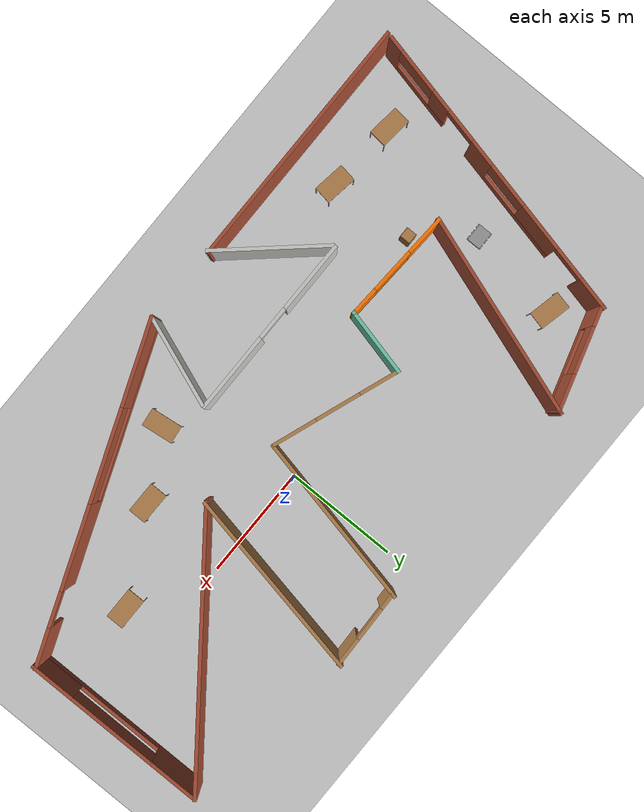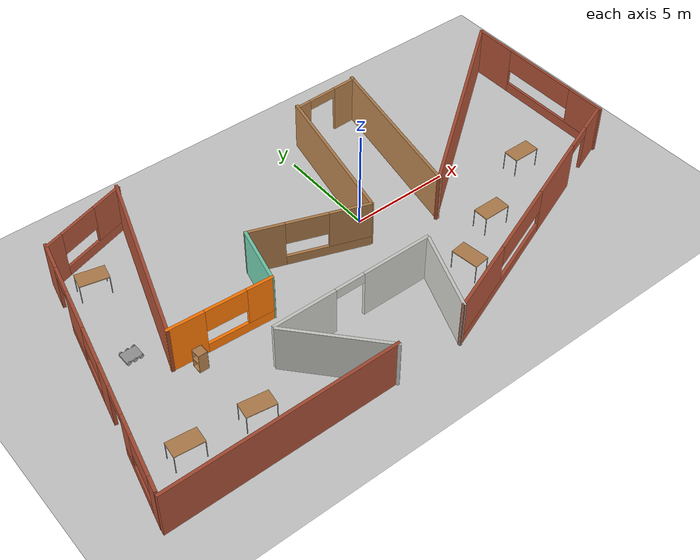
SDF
<sdf version="1.6">
 <world name="default">
  <plugin name="welcome_message" filename="libwelcome_message.so"/>
  <light name="sun" type="directional">
   <pose>0 0 10 0 -0 0</pose>
   <diffuse>0.8 0.8 0.8 1</diffuse>
   <specular>0.1 0.1 0.1 1</specular>
   <attenuation>
    <range>1000</range>
    <constant>0.9</constant>
    <linear>0.01</linear>
    <quadratic>0.001</quadratic>
   </attenuation>
   <direction>-0.5 0.5 -1</direction>
  </light>
  <model name="ground_plane">
   <static>1</static>
   <link name="link">
    <collision name="collision">
     <geometry><plane><normal>0 0 1</normal><size>100 100</size></plane></geometry>
     <surface><friction><ode><mu>100</mu><mu2>50</mu2></ode></friction></surface>
    </collision>
    <visual name="visual">
     <cast_shadows>0</cast_shadows>
     <geometry><plane><normal>0 0 1</normal><size>100 100</size></plane></geometry>
     <material>
      <script><uri>file://media/materials/scripts/gazebo.material</uri><name>Gazebo/Grey</name></script>
     </material>
    </visual>
   </link>
  </model>
  <gravity>0 0 -9.8</gravity>
  <magnetic_field>6e-06 2.3e-05 -4.2e-05</magnetic_field>
  <atmosphere type="adiabatic"/>
  <physics name="default_physics" default="0" type="ode">
   <max_step_size>0.001</max_step_size>
   <real_time_factor>1</real_time_factor>
   <real_time_update_rate>1000</real_time_update_rate>
  </physics>
  <scene><ambient>0.4 0.4 0.4 1</ambient><background>0.7 0.7 0.7 1</background><shadows>1</shadows></scene>
  <spherical_coordinates>
   <surface_model>EARTH_WGS84</surface_model>
   <latitude_deg>0</latitude_deg>
   <longitude_deg>0</longitude_deg>
   <elevation>0</elevation>
   <heading_deg>0</heading_deg>
  </spherical_coordinates>
  <model name="my_building">
   <pose>-1.82357 -0.88162 0 0 -0 0</pose>
   <link name="Wall_10">
    <pose>-7.20518 -1.23967 0 0 0 -0.053362</pose>
    <visual name="Wall_10_Visual_0">
     <pose>-1.65873 0 1.25 0 -0 0</pose>
     <geometry><box><size>1.79088 0.15 2.5</size></box></geometry>
     <material>
      <script><uri>file://media/materials/scripts/gazebo.material</uri><name>Gazebo/Grey</name></script>
      <ambient>0.996078 0.47451 0.0196078 1</ambient>
     </material>
    </visual>
    <collision name="Wall_10_Collision_0">
     <geometry><box><size>1.79088 0.15 2.5</size></box></geometry>
     <pose>-1.65873 0 1.25 0 -0 0</pose>
    </collision>
    <visual name="Wall_10_Visual_1">
     <pose>0.895442 0 0.25 0 -0 0</pose>
     <geometry><box><size>3.31746 0.15 0.5</size></box></geometry>
     <material>
      <script><uri>file://media/materials/scripts/gazebo.material</uri><name>Gazebo/Grey</name></script>
      <ambient>0.996078 0.47451 0.0196078 1</ambient>
     </material>
    </visual>
    <collision name="Wall_10_Collision_1">
     <geometry><box><size>3.31746 0.15 0.5</size></box></geometry>
     <pose>0.895442 0 0.25 0 -0 0</pose>
    </collision>
    <visual name="Wall_10_Visual_2">
     <pose>1.89544 0 1.5 0 -0 0</pose>
     <geometry><box><size>1.31746 0.15 2</size></box></geometry>
     <material>
      <script><uri>file://media/materials/scripts/gazebo.material</uri><name>Gazebo/Grey</name></script>
      <ambient>0.996078 0.47451 0.0196078 1</ambient>
     </material>
    </visual>
    <collision name="Wall_10_Collision_2">
     <geometry><box><size>1.31746 0.15 2</size></box></geometry>
     <pose>1.89544 0 1.5 0 -0 0</pose>
    </collision>
    <visual name="Wall_10_Visual_3">
     <pose>0.236711 0 1.9 0 -0 0</pose>
     <geometry><box><size>2 0.15 1.2</size></box></geometry>
     <material>
      <script><uri>file://media/materials/scripts/gazebo.material</uri><name>Gazebo/Grey</name></script>
      <ambient>0.996078 0.47451 0.0196078 1</ambient>
     </material>
    </visual>
    <collision name="Wall_10_Collision_3">
     <geometry><box><size>2 0.15 1.2</size></box></geometry>
     <pose>0.236711 0 1.9 0 -0 0</pose>
    </collision>
   </link>
   <link name="Wall_11">
    <collision name="Wall_11_Collision">
     <geometry><box><size>3.02948 0.15 2.5</size></box></geometry>
     <pose>0 0 1.25 0 -0 0</pose>
    </collision>
    <visual name="Wall_11_Visual">
     <pose>0 0 1.25 0 -0 0</pose>
     <geometry><box><size>3.02948 0.15 2.5</size></box></geometry>
     <material>
      <script><uri>file://media/materials/scripts/gazebo.material</uri><name>Gazebo/Grey</name></script>
      <ambient>0.435294 0.796078 0.67451 1</ambient>
     </material>
    </visual>
    <pose>-4.3944 0.028361 0 0 -0 1.33612</pose>
   </link>
   <link name="Wall_12">
    <pose>-1.39731 0.461222 0 0 0 -0.348539</pose>
    <visual name="Wall_12_Visual_0">
     <pose>-1.99563 0 1.25 0 -0 0</pose>
     <geometry><box><size>1.82401 0.15 2.5</size></box></geometry>
     <material>
      <script><uri>file://media/materials/scripts/gazebo.material</uri><name>Gazebo/Wood</name></script>
      <ambient>0.435294 0.796078 0.67451 1</ambient>
     </material>
    </visual>
    <collision name="Wall_12_Collision_0">
     <geometry><box><size>1.82401 0.15 2.5</size></box></geometry>
     <pose>-1.99563 0 1.25 0 -0 0</pose>
    </collision>
    <visual name="Wall_12_Visual_1">
     <pose>0.912006 0 0.25 0 -0 0</pose>
     <geometry><box><size>3.99125 0.15 0.5</size></box></geometry>
     <material>
      <script><uri>file://media/materials/scripts/gazebo.material</uri><name>Gazebo/Wood</name></script>
      <ambient>0.435294 0.796078 0.67451 1</ambient>
     </material>
    </visual>
    <collision name="Wall_12_Collision_1">
     <geometry><box><size>3.99125 0.15 0.5</size></box></geometry>
     <pose>0.912006 0 0.25 0 -0 0</pose>
    </collision>
    <visual name="Wall_12_Visual_2">
     <pose>1.91201 0 1.5 0 -0 0</pose>
     <geometry><box><size>1.99125 0.15 2</size></box></geometry>
     <material>
      <script><uri>file://media/materials/scripts/gazebo.material</uri><name>Gazebo/Wood</name></script>
      <ambient>0.435294 0.796078 0.67451 1</ambient>
     </material>
    </visual>
    <collision name="Wall_12_Collision_2">
     <geometry><box><size>1.99125 0.15 2</size></box></geometry>
     <pose>1.91201 0 1.5 0 -0 0</pose>
    </collision>
    <visual name="Wall_12_Visual_3">
     <pose>-0.083621 0 1.9 0 -0 0</pose>
     <geometry><box><size>2 0.15 1.2</size></box></geometry>
     <material>
      <script><uri>file://media/materials/scripts/gazebo.material</uri><name>Gazebo/Wood</name></script>
      <ambient>0.435294 0.796078 0.67451 1</ambient>
     </material>
    </visual>
    <collision name="Wall_12_Collision_3">
     <geometry><box><size>2 0.15 1.2</size></box></geometry>
     <pose>-0.083621 0 1.9 0 -0 0</pose>
    </collision>
   </link>
   <link name="Wall_13">
    <collision name="Wall_13_Collision">
     <geometry><box><size>7.73883 0.15 2.5</size></box></geometry>
     <pose>0 0 1.25 0 -0 0</pose>
    </collision>
    <visual name="Wall_13_Visual">
     <pose>0 0 1.25 0 -0 0</pose>
     <geometry><box><size>7.73883 0.15 2.5</size></box></geometry>
     <material>
      <script><uri>file://media/materials/scripts/gazebo.material</uri><name>Gazebo/Wood</name></script>
      <ambient>0.435294 0.796078 0.67451 1</ambient>
     </material>
    </visual>
    <pose>2.1093 3.20845 0 0 -0 1.36539</pose>
   </link>
   <link name="Wall_14">
    <pose>4.60393 6.87033 0 0 -0 0.030657</pose>
    <visual name="Wall_14_Visual_0">
     <pose>-1.41036 0 1.25 0 -0 0</pose>
     <geometry><box><size>0.772303 0.15 2.5</size></box></geometry>
     <material>
      <script><uri>file://media/materials/scripts/gazebo.material</uri><name>Gazebo/Wood</name></script>
      <ambient>1 1 1 1</ambient>
     </material>
    </visual>
    <collision name="Wall_14_Collision_0">
     <geometry><box><size>0.772303 0.15 2.5</size></box></geometry>
     <pose>-1.41036 0 1.25 0 -0 0</pose>
    </collision>
    <visual name="Wall_14_Visual_1">
     <pose>1.13615 0 1.25 0 -0 0</pose>
     <geometry><box><size>1.32072 0.15 2.5</size></box></geometry>
     <material>
      <script><uri>file://media/materials/scripts/gazebo.material</uri><name>Gazebo/Wood</name></script>
      <ambient>1 1 1 1</ambient>
     </material>
    </visual>
    <collision name="Wall_14_Collision_1">
     <geometry><box><size>1.32072 0.15 2.5</size></box></geometry>
     <pose>1.13615 0 1.25 0 -0 0</pose>
    </collision>
    <visual name="Wall_14_Visual_2">
     <pose>-0.27421 0 2.25 0 -0 0</pose>
     <geometry><box><size>1.5 0.15 0.5</size></box></geometry>
     <material>
      <script><uri>file://media/materials/scripts/gazebo.material</uri><name>Gazebo/Wood</name></script>
      <ambient>1 1 1 1</ambient>
     </material>
    </visual>
    <collision name="Wall_14_Collision_2">
     <geometry><box><size>1.5 0.15 0.5</size></box></geometry>
     <pose>-0.27421 0 2.25 0 -0 0</pose>
    </collision>
   </link>
   <link name="Wall_15">
    <collision name="Wall_15_Collision">
     <geometry><box><size>8.47447 0.15 2.5</size></box></geometry>
     <pose>0 0 1.25 0 -0 0</pose>
    </collision>
    <visual name="Wall_15_Visual">
     <pose>0 0 1.25 0 -0 0</pose>
     <geometry><box><size>8.47447 0.15 2.5</size></box></geometry>
     <material>
      <script><uri>file://media/materials/scripts/gazebo.material</uri><name>Gazebo/Wood</name></script>
      <ambient>1 1 1 1</ambient>
     </material>
    </visual>
    <pose>5.55071 2.93899 0 0 0 -1.75783</pose>
   </link>
   <link name="Wall_16">
    <collision name="Wall_16_Collision">
     <geometry><box><size>11.8484 0.15 2.5</size></box></geometry>
     <pose>0 0 1.25 0 -0 0</pose>
    </collision>
    <visual name="Wall_16_Visual">
     <pose>0 0 1.25 0 -0 0</pose>
     <geometry><box><size>11.8484 0.15 2.5</size></box></geometry>
     <material>
      <script><uri>file://media/materials/scripts/gazebo.material</uri><name>Gazebo/Bricks</name></script>
      <ambient>0.760784 0.662745 0.627451 1</ambient>
     </material>
    </visual>
    <pose>9.36619 2.38481 0 0 -0 0.649059</pose>
   </link>
   <link name="Wall_17">
    <pose>14.026 1.76474 0 0 0 -1.5708</pose>
    <visual name="Wall_17_Visual_0">
     <pose>-3.02356 0 1.25 0 -0 0</pose>
     <geometry><box><size>2.20289 0.15 2.5</size></box></geometry>
     <material>
      <script><uri>file://media/materials/scripts/gazebo.material</uri><name>Gazebo/Bricks</name></script>
      <ambient>0.760784 0.662745 0.627451 1</ambient>
     </material>
    </visual>
    <collision name="Wall_17_Collision_0">
     <geometry><box><size>2.20289 0.15 2.5</size></box></geometry>
     <pose>-3.02356 0 1.25 0 -0 0</pose>
    </collision>
    <visual name="Wall_17_Visual_1">
     <pose>1.10144 0 0.25 0 -0 0</pose>
     <geometry><box><size>6.04711 0.15 0.5</size></box></geometry>
     <material>
      <script><uri>file://media/materials/scripts/gazebo.material</uri><name>Gazebo/Bricks</name></script>
      <ambient>0.760784 0.662745 0.627451 1</ambient>
     </material>
    </visual>
    <collision name="Wall_17_Collision_1">
     <geometry><box><size>6.04711 0.15 0.5</size></box></geometry>
     <pose>1.10144 0 0.25 0 -0 0</pose>
    </collision>
    <visual name="Wall_17_Visual_2">
     <pose>3.10144 0 1.5 0 -0 0</pose>
     <geometry><box><size>2.04711 0.15 2</size></box></geometry>
     <material>
      <script><uri>file://media/materials/scripts/gazebo.material</uri><name>Gazebo/Bricks</name></script>
      <ambient>0.760784 0.662745 0.627451 1</ambient>
     </material>
    </visual>
    <collision name="Wall_17_Collision_2">
     <geometry><box><size>2.04711 0.15 2</size></box></geometry>
     <pose>3.10144 0 1.5 0 -0 0</pose>
    </collision>
    <visual name="Wall_17_Visual_3">
     <pose>0.077887 0 1.9 0 -0 0</pose>
     <geometry><box><size>4 0.15 1.2</size></box></geometry>
     <material>
      <script><uri>file://media/materials/scripts/gazebo.material</uri><name>Gazebo/Bricks</name></script>
      <ambient>0.760784 0.662745 0.627451 1</ambient>
     </material>
    </visual>
    <collision name="Wall_17_Collision_3">
     <geometry><box><size>4 0.15 1.2</size></box></geometry>
     <pose>0.077887 0 1.9 0 -0 0</pose>
    </collision>
   </link>
   <link name="Wall_18">
    <pose>7.23317 -4.80054 0 0 0 -2.77337</pose>
    <visual name="Wall_18_Visual_0">
     <pose>-6.47131 0 1.25 0 -0 0</pose>
     <geometry><box><size>1.76906 0.15 2.5</size></box></geometry>
     <material>
      <script><uri>file://media/materials/scripts/gazebo.material</uri><name>Gazebo/Bricks</name></script>
      <ambient>0.760784 0.662745 0.627451 1</ambient>
     </material>
    </visual>
    <collision name="Wall_18_Collision_0">
     <geometry><box><size>1.76906 0.15 2.5</size></box></geometry>
     <pose>-6.47131 0 1.25 0 -0 0</pose>
    </collision>
    <visual name="Wall_18_Visual_1">
     <pose>-2.27515 0 1.25 0 -0 0</pose>
     <geometry><box><size>3.62326 0.15 2.5</size></box></geometry>
     <material>
      <script><uri>file://media/materials/scripts/gazebo.material</uri><name>Gazebo/Bricks</name></script>
      <ambient>0.760784 0.662745 0.627451 1</ambient>
     </material>
    </visual>
    <collision name="Wall_18_Collision_1">
     <geometry><box><size>3.62326 0.15 2.5</size></box></geometry>
     <pose>-2.27515 0 1.25 0 -0 0</pose>
    </collision>
    <visual name="Wall_18_Visual_2">
     <pose>3.44616 0 0.25 0 -0 0</pose>
     <geometry><box><size>7.81937 0.15 0.5</size></box></geometry>
     <material>
      <script><uri>file://media/materials/scripts/gazebo.material</uri><name>Gazebo/Bricks</name></script>
      <ambient>0.760784 0.662745 0.627451 1</ambient>
     </material>
    </visual>
    <collision name="Wall_18_Collision_2">
     <geometry><box><size>7.81937 0.15 0.5</size></box></geometry>
     <pose>3.44616 0 0.25 0 -0 0</pose>
    </collision>
    <visual name="Wall_18_Visual_3">
     <pose>5.44616 0 1.5 0 -0 0</pose>
     <geometry><box><size>3.81937 0.15 2</size></box></geometry>
     <material>
      <script><uri>file://media/materials/scripts/gazebo.material</uri><name>Gazebo/Bricks</name></script>
      <ambient>0.760784 0.662745 0.627451 1</ambient>
     </material>
    </visual>
    <collision name="Wall_18_Collision_3">
     <geometry><box><size>3.81937 0.15 2</size></box></geometry>
     <pose>5.44616 0 1.5 0 -0 0</pose>
    </collision>
    <visual name="Wall_18_Visual_4">
     <pose>1.53648 0 1.9 0 -0 0</pose>
     <geometry><box><size>4 0.15 1.2</size></box></geometry>
     <material>
      <script><uri>file://media/materials/scripts/gazebo.material</uri><name>Gazebo/Bricks</name></script>
      <ambient>0.760784 0.662745 0.627451 1</ambient>
     </material>
    </visual>
    <collision name="Wall_18_Collision_4">
     <geometry><box><size>4 0.15 1.2</size></box></geometry>
     <pose>1.53648 0 1.9 0 -0 0</pose>
    </collision>
    <visual name="Wall_18_Visual_5">
     <pose>-4.83679 0 2.25 0 -0 0</pose>
     <geometry><box><size>1.5 0.15 0.5</size></box></geometry>
     <material>
      <script><uri>file://media/materials/scripts/gazebo.material</uri><name>Gazebo/Bricks</name></script>
      <ambient>0.760784 0.662745 0.627451 1</ambient>
     </material>
    </visual>
    <collision name="Wall_18_Collision_5">
     <geometry><box><size>1.5 0.15 0.5</size></box></geometry>
     <pose>-4.83679 0 2.25 0 -0 0</pose>
    </collision>
   </link>
   <link name="Wall_19">
    <collision name="Wall_19_Collision">
     <geometry><box><size>4.1326 0.15 2.5</size></box></geometry>
     <pose>0 0 1.25 0 -0 0</pose>
    </collision>
    <visual name="Wall_19_Visual">
     <pose>0 0 1.25 0 -0 0</pose>
     <geometry><box><size>4.1326 0.15 2.5</size></box></geometry>
     <material>
      <script><uri>file://media/materials/scripts/gazebo.material</uri><name>Gazebo/CeilingTiled</name></script>
      <ambient>1 1 1 1</ambient>
     </material>
    </visual>
    <pose>1.14396 -5.5585 0 0 -0 1.20967</pose>
   </link>
   <link name="Wall_20">
    <pose>-2.20247 -3.5901 0 0 -0 3.14159</pose>
    <visual name="Wall_20_Visual_0">
     <pose>-2.34523 0 1.25 0 -0 0</pose>
     <geometry><box><size>3.55955 0.15 2.5</size></box></geometry>
     <material>
      <script><uri>file://media/materials/scripts/gazebo.material</uri><name>Gazebo/CeilingTiled</name></script>
      <ambient>0.921569 0.807843 0.615686 1</ambient>
     </material>
    </visual>
    <collision name="Wall_20_Collision_0">
     <geometry><box><size>3.55955 0.15 2.5</size></box></geometry>
     <pose>-2.34523 0 1.25 0 -0 0</pose>
    </collision>
    <visual name="Wall_20_Visual_1">
     <pose>2.52977 0 1.25 0 -0 0</pose>
     <geometry><box><size>3.19045 0.15 2.5</size></box></geometry>
     <material>
      <script><uri>file://media/materials/scripts/gazebo.material</uri><name>Gazebo/CeilingTiled</name></script>
      <ambient>0.921569 0.807843 0.615686 1</ambient>
     </material>
    </visual>
    <collision name="Wall_20_Collision_1">
     <geometry><box><size>3.19045 0.15 2.5</size></box></geometry>
     <pose>2.52977 0 1.25 0 -0 0</pose>
    </collision>
    <visual name="Wall_20_Visual_2">
     <pose>0.184548 0 2.25 0 -0 0</pose>
     <geometry><box><size>1.5 0.15 0.5</size></box></geometry>
     <material>
      <script><uri>file://media/materials/scripts/gazebo.material</uri><name>Gazebo/CeilingTiled</name></script>
      <ambient>0.921569 0.807843 0.615686 1</ambient>
     </material>
    </visual>
    <collision name="Wall_20_Collision_2">
     <geometry><box><size>1.5 0.15 0.5</size></box></geometry>
     <pose>0.184548 0 2.25 0 -0 0</pose>
    </collision>
   </link>
   <link name="Wall_21">
    <collision name="Wall_21_Collision">
     <geometry><box><size>5.09839 0.15 2.5</size></box></geometry>
     <pose>0 0 1.25 0 -0 0</pose>
    </collision>
    <visual name="Wall_21_Visual">
     <pose>0 0 1.25 0 -0 0</pose>
     <geometry><box><size>5.09839 0.15 2.5</size></box></geometry>
     <material>
      <script><uri>file://media/materials/scripts/gazebo.material</uri><name>Gazebo/CeilingTiled</name></script>
      <ambient>0.921569 0.807843 0.615686 1</ambient>
     </material>
    </visual>
    <pose>-4.60426 -5.54091 0 0 0 -0.841746</pose>
   </link>
   <link name="Wall_22">
    <collision name="Wall_22_Collision">
     <geometry><box><size>11.25 0.15 2.5</size></box></geometry>
     <pose>0 0 1.25 0 -0 0</pose>
    </collision>
    <visual name="Wall_22_Visual">
     <pose>0 0 1.25 0 -0 0</pose>
     <geometry><box><size>11.25 0.15 2.5</size></box></geometry>
     <material>
      <script><uri>file://media/materials/scripts/gazebo.material</uri><name>Gazebo/Bricks</name></script>
      <ambient>0.996078 0.47451 0.0196078 1</ambient>
     </material>
    </visual>
    <pose>-8.50604 -7.31583 0 0 -0 3.14159</pose>
   </link>
   <link name="Wall_7">
    <pose>-12.5684 -0.491172 0 0 -0 1.35294</pose>
    <visual name="Wall_7_Visual_0">
     <pose>-6.46291 0 1.25 0 -0 0</pose>
     <geometry><box><size>0.733183 0.15 2.5</size></box></geometry>
     <material>
      <script><uri>file://media/materials/scripts/gazebo.material</uri><name>Gazebo/Bricks</name></script>
      <ambient>0.996078 0.47451 0.0196078 1</ambient>
     </material>
    </visual>
    <collision name="Wall_7_Collision_0">
     <geometry><box><size>0.733183 0.15 2.5</size></box></geometry>
     <pose>-6.46291 0 1.25 0 -0 0</pose>
    </collision>
    <visual name="Wall_7_Visual_1">
     <pose>-0.982571 0 1.25 0 -0 0</pose>
     <geometry><box><size>1.23194 0.15 2.5</size></box></geometry>
     <material>
      <script><uri>file://media/materials/scripts/gazebo.material</uri><name>Gazebo/Bricks</name></script>
      <ambient>0.996078 0.47451 0.0196078 1</ambient>
     </material>
    </visual>
    <collision name="Wall_7_Collision_1">
     <geometry><box><size>1.23194 0.15 2.5</size></box></geometry>
     <pose>-0.982571 0 1.25 0 -0 0</pose>
    </collision>
    <visual name="Wall_7_Visual_2">
     <pose>6.05834 0 1.25 0 -0 0</pose>
     <geometry><box><size>1.54232 0.15 2.5</size></box></geometry>
     <material>
      <script><uri>file://media/materials/scripts/gazebo.material</uri><name>Gazebo/Bricks</name></script>
      <ambient>0.996078 0.47451 0.0196078 1</ambient>
     </material>
    </visual>
    <collision name="Wall_7_Collision_2">
     <geometry><box><size>1.54232 0.15 2.5</size></box></geometry>
     <pose>6.05834 0 1.25 0 -0 0</pose>
    </collision>
    <visual name="Wall_7_Visual_3">
     <pose>-4.59743 0 0.25 0 -0 0</pose>
     <geometry><box><size>2.99777 0.15 0.5</size></box></geometry>
     <material>
      <script><uri>file://media/materials/scripts/gazebo.material</uri><name>Gazebo/Bricks</name></script>
      <ambient>0.996078 0.47451 0.0196078 1</ambient>
     </material>
    </visual>
    <collision name="Wall_7_Collision_3">
     <geometry><box><size>2.99777 0.15 0.5</size></box></geometry>
     <pose>-4.59743 0 0.25 0 -0 0</pose>
    </collision>
    <visual name="Wall_7_Visual_4">
     <pose>1.71029 0 0.25 0 -0 0</pose>
     <geometry><box><size>4.15378 0.15 0.5</size></box></geometry>
     <material>
      <script><uri>file://media/materials/scripts/gazebo.material</uri><name>Gazebo/Bricks</name></script>
      <ambient>0.996078 0.47451 0.0196078 1</ambient>
     </material>
    </visual>
    <collision name="Wall_7_Collision_4">
     <geometry><box><size>4.15378 0.15 0.5</size></box></geometry>
     <pose>1.71029 0 0.25 0 -0 0</pose>
    </collision>
    <visual name="Wall_7_Visual_5">
     <pose>-3.59743 0 1.5 0 -0 0</pose>
     <geometry><box><size>0.997774 0.15 2</size></box></geometry>
     <material>
      <script><uri>file://media/materials/scripts/gazebo.material</uri><name>Gazebo/Bricks</name></script>
      <ambient>0.996078 0.47451 0.0196078 1</ambient>
     </material>
    </visual>
    <collision name="Wall_7_Collision_5">
     <geometry><box><size>0.997774 0.15 2</size></box></geometry>
     <pose>-3.59743 0 1.5 0 -0 0</pose>
    </collision>
    <visual name="Wall_7_Visual_6">
     <pose>-3.59743 0 1.5 0 -0 0</pose>
     <geometry><box><size>0.997774 0.15 2</size></box></geometry>
     <material>
      <script><uri>file://media/materials/scripts/gazebo.material</uri><name>Gazebo/Bricks</name></script>
      <ambient>0.996078 0.47451 0.0196078 1</ambient>
     </material>
    </visual>
    <collision name="Wall_7_Collision_6">
     <geometry><box><size>0.997774 0.15 2</size></box></geometry>
     <pose>-3.59743 0 1.5 0 -0 0</pose>
    </collision>
    <visual name="Wall_7_Visual_7">
     <pose>2.71029 0 1.5 0 -0 0</pose>
     <geometry><box><size>2.15378 0.15 2</size></box></geometry>
     <material>
      <script><uri>file://media/materials/scripts/gazebo.material</uri><name>Gazebo/Bricks</name></script>
      <ambient>0.996078 0.47451 0.0196078 1</ambient>
     </material>
    </visual>
    <collision name="Wall_7_Collision_7">
     <geometry><box><size>2.15378 0.15 2</size></box></geometry>
     <pose>2.71029 0 1.5 0 -0 0</pose>
    </collision>
    <visual name="Wall_7_Visual_8">
     <pose>-5.09631 0 1.9 0 -0 0</pose>
     <geometry><box><size>2 0.15 1.2</size></box></geometry>
     <material>
      <script><uri>file://media/materials/scripts/gazebo.material</uri><name>Gazebo/Bricks</name></script>
      <ambient>0.996078 0.47451 0.0196078 1</ambient>
     </material>
    </visual>
    <collision name="Wall_7_Collision_8">
     <geometry><box><size>2 0.15 1.2</size></box></geometry>
     <pose>-5.09631 0 1.9 0 -0 0</pose>
    </collision>
    <visual name="Wall_7_Visual_9">
     <pose>0.633398 0 1.9 0 -0 0</pose>
     <geometry><box><size>2 0.15 1.2</size></box></geometry>
     <material>
      <script><uri>file://media/materials/scripts/gazebo.material</uri><name>Gazebo/Bricks</name></script>
      <ambient>0.996078 0.47451 0.0196078 1</ambient>
     </material>
    </visual>
    <collision name="Wall_7_Collision_9">
     <geometry><box><size>2 0.15 1.2</size></box></geometry>
     <pose>0.633398 0 1.9 0 -0 0</pose>
    </collision>
    <visual name="Wall_7_Visual_10">
     <pose>-2.34854 0 2.25 0 -0 0</pose>
     <geometry><box><size>1.5 0.15 0.5</size></box></geometry>
     <material>
      <script><uri>file://media/materials/scripts/gazebo.material</uri><name>Gazebo/Bricks</name></script>
      <ambient>0.996078 0.47451 0.0196078 1</ambient>
     </material>
    </visual>
    <collision name="Wall_7_Collision_10">
     <geometry><box><size>1.5 0.15 0.5</size></box></geometry>
     <pose>-2.34854 0 2.25 0 -0 0</pose>
    </collision>
    <visual name="Wall_7_Visual_11">
     <pose>-2.34854 0 2.25 0 -0 0</pose>
     <geometry><box><size>1.5 0.15 0.5</size></box></geometry>
     <material>
      <script><uri>file://media/materials/scripts/gazebo.material</uri><name>Gazebo/Bricks</name></script>
      <ambient>0.996078 0.47451 0.0196078 1</ambient>
     </material>
    </visual>
    <collision name="Wall_7_Collision_11">
     <geometry><box><size>1.5 0.15 0.5</size></box></geometry>
     <pose>-2.34854 0 2.25 0 -0 0</pose>
    </collision>
    <visual name="Wall_7_Visual_12">
     <pose>4.53718 0 2.25 0 -0 0</pose>
     <geometry><box><size>1.5 0.15 0.5</size></box></geometry>
     <material>
      <script><uri>file://media/materials/scripts/gazebo.material</uri><name>Gazebo/Bricks</name></script>
      <ambient>0.996078 0.47451 0.0196078 1</ambient>
     </material>
    </visual>
    <collision name="Wall_7_Collision_12">
     <geometry><box><size>1.5 0.15 0.5</size></box></geometry>
     <pose>4.53718 0 2.25 0 -0 0</pose>
    </collision>
   </link>
   <link name="Wall_8">
    <pose>-8.97514 6.65806 0 0 -0 0.299999</pose>
    <visual name="Wall_8_Visual_0">
     <pose>-1.83868 0 1.25 0 -0 0</pose>
     <geometry><box><size>0.938894 0.15 2.5</size></box></geometry>
     <material>
      <script><uri>file://media/materials/scripts/gazebo.material</uri><name>Gazebo/Bricks</name></script>
      <ambient>0.996078 0.47451 0.0196078 1</ambient>
     </material>
    </visual>
    <collision name="Wall_8_Collision_0">
     <geometry><box><size>0.938894 0.15 2.5</size></box></geometry>
     <pose>-1.83868 0 1.25 0 -0 0</pose>
    </collision>
    <visual name="Wall_8_Visual_1">
     <pose>0.469447 0 0.25 0 -0 0</pose>
     <geometry><box><size>3.67735 0.15 0.5</size></box></geometry>
     <material>
      <script><uri>file://media/materials/scripts/gazebo.material</uri><name>Gazebo/Bricks</name></script>
      <ambient>0.996078 0.47451 0.0196078 1</ambient>
     </material>
    </visual>
    <collision name="Wall_8_Collision_1">
     <geometry><box><size>3.67735 0.15 0.5</size></box></geometry>
     <pose>0.469447 0 0.25 0 -0 0</pose>
    </collision>
    <visual name="Wall_8_Visual_2">
     <pose>1.46945 0 1.5 0 -0 0</pose>
     <geometry><box><size>1.67735 0.15 2</size></box></geometry>
     <material>
      <script><uri>file://media/materials/scripts/gazebo.material</uri><name>Gazebo/Bricks</name></script>
      <ambient>0.996078 0.47451 0.0196078 1</ambient>
     </material>
    </visual>
    <collision name="Wall_8_Collision_2">
     <geometry><box><size>1.67735 0.15 2</size></box></geometry>
     <pose>1.46945 0 1.5 0 -0 0</pose>
    </collision>
    <visual name="Wall_8_Visual_3">
     <pose>-0.369229 0 1.9 0 -0 0</pose>
     <geometry><box><size>2 0.15 1.2</size></box></geometry>
     <material>
      <script><uri>file://media/materials/scripts/gazebo.material</uri><name>Gazebo/Bricks</name></script>
      <ambient>0.996078 0.47451 0.0196078 1</ambient>
     </material>
    </visual>
    <collision name="Wall_8_Collision_3">
     <geometry><box><size>2 0.15 1.2</size></box></geometry>
     <pose>-0.369229 0 1.9 0 -0 0</pose>
    </collision>
   </link>
   <link name="Wall_9">
    <collision name="Wall_9_Collision">
     <geometry><box><size>9.16616 0.15 2.5</size></box></geometry>
     <pose>0 0 1.25 0 -0 0</pose>
    </collision>
    <visual name="Wall_9_Visual">
     <pose>0 0 1.25 0 -0 0</pose>
     <geometry><box><size>9.16616 0.15 2.5</size></box></geometry>
     <material>
      <script><uri>file://media/materials/scripts/gazebo.material</uri><name>Gazebo/Bricks</name></script>
      <ambient>0.921569 0.807843 0.615686 1</ambient>
     </material>
    </visual>
    <pose>-8.26146 3.14483 0 0 0 -1.89117</pose>
   </link>
   <static>1</static>
  </model>
  <model name="table">
   <static>0</static>
   <link name="link">
    <collision name="surface">
     <pose>0 0 1 0 -0 0</pose>
     <geometry><box><size>1.5 0.8 0.03</size></box></geometry>
     <surface><friction><ode><mu>0.6</mu><mu2>0.6</mu2></ode></friction></surface>
    </collision>
    <visual name="visual1">
     <pose>0 0 1 0 -0 0</pose>
     <geometry><box><size>1.4 0.8 0.04</size></box></geometry>
     <material>
      <script><uri>file://media/materials/scripts/gazebo.material</uri><name>Gazebo/Wood</name></script>
     </material>
    </visual>
    <collision name="front_left_leg">
     <pose>0.68 0.38 0.5 0 -0 0</pose>
     <geometry><cylinder><radius>0.02</radius><length>1</length></cylinder></geometry>
    </collision>
    <visual name="front_left_leg">
     <pose>0.68 0.38 0.5 0 -0 0</pose>
     <geometry><cylinder><radius>0.02</radius><length>1</length></cylinder></geometry>
     <material>
      <script><uri>file://media/materials/scripts/gazebo.material</uri><name>Gazebo/Grey</name></script>
     </material>
    </visual>
    <collision name="front_right_leg">
     <pose>0.68 -0.38 0.5 0 -0 0</pose>
     <geometry><cylinder><radius>0.02</radius><length>1</length></cylinder></geometry>
    </collision>
    <visual name="front_right_leg">
     <pose>0.68 -0.38 0.5 0 -0 0</pose>
     <geometry><cylinder><radius>0.02</radius><length>1</length></cylinder></geometry>
     <material>
      <script><uri>file://media/materials/scripts/gazebo.material</uri><name>Gazebo/Grey</name></script>
     </material>
    </visual>
    <collision name="back_right_leg">
     <pose>-0.68 -0.38 0.5 0 -0 0</pose>
     <geometry><cylinder><radius>0.02</radius><length>1</length></cylinder></geometry>
    </collision>
    <visual name="back_right_leg">
     <pose>-0.68 -0.38 0.5 0 -0 0</pose>
     <geometry><cylinder><radius>0.02</radius><length>1</length></cylinder></geometry>
     <material>
      <script><uri>file://media/materials/scripts/gazebo.material</uri><name>Gazebo/Grey</name></script>
     </material>
    </visual>
    <collision name="back_left_leg">
     <pose>-0.68 0.38 0.5 0 -0 0</pose>
     <geometry><cylinder><radius>0.02</radius><length>1</length></cylinder></geometry>
    </collision>
    <visual name="back_left_leg">
     <pose>-0.68 0.38 0.5 0 -0 0</pose>
     <geometry><cylinder><radius>0.02</radius><length>1</length></cylinder></geometry>
     <material>
      <script><uri>file://media/materials/scripts/gazebo.material</uri><name>Gazebo/Grey</name></script>
     </material>
    </visual>
    <inertial>
     <inertia><ixx>1</ixx><ixy>0</ixy><ixz>0</ixz><iyy>1</iyy><iyz>0</iyz><izz>1</izz></inertia>
     <mass>1</mass>
    </inertial>
   </link>
   <pose>-10.2213 -6.20555 -1e-06 -2e-06 -0 -0.150803</pose>
  </model>
  <model name="table_0">
   <static>0</static>
   <link name="link">
    <collision name="surface">
     <pose>0 0 1 0 -0 0</pose>
     <geometry><box><size>1.5 0.8 0.03</size></box></geometry>
     <surface><friction><ode><mu>0.6</mu><mu2>0.6</mu2></ode></friction></surface>
    </collision>
    <visual name="visual1">
     <pose>0 0 1 0 -0 0</pose>
     <geometry><box><size>1.4 0.8 0.04</size></box></geometry>
     <material>
      <script><uri>file://media/materials/scripts/gazebo.material</uri><name>Gazebo/Wood</name></script>
     </material>
    </visual>
    <collision name="front_left_leg">
     <pose>0.68 0.38 0.5 0 -0 0</pose>
     <geometry><cylinder><radius>0.02</radius><length>1</length></cylinder></geometry>
    </collision>
    <visual name="front_left_leg">
     <pose>0.68 0.38 0.5 0 -0 0</pose>
     <geometry><cylinder><radius>0.02</radius><length>1</length></cylinder></geometry>
     <material>
      <script><uri>file://media/materials/scripts/gazebo.material</uri><name>Gazebo/Grey</name></script>
     </material>
    </visual>
    <collision name="front_right_leg">
     <pose>0.68 -0.38 0.5 0 -0 0</pose>
     <geometry><cylinder><radius>0.02</radius><length>1</length></cylinder></geometry>
    </collision>
    <visual name="front_right_leg">
     <pose>0.68 -0.38 0.5 0 -0 0</pose>
     <geometry><cylinder><radius>0.02</radius><length>1</length></cylinder></geometry>
     <material>
      <script><uri>file://media/materials/scripts/gazebo.material</uri><name>Gazebo/Grey</name></script>
     </material>
    </visual>
    <collision name="back_right_leg">
     <pose>-0.68 -0.38 0.5 0 -0 0</pose>
     <geometry><cylinder><radius>0.02</radius><length>1</length></cylinder></geometry>
    </collision>
    <visual name="back_right_leg">
     <pose>-0.68 -0.38 0.5 0 -0 0</pose>
     <geometry><cylinder><radius>0.02</radius><length>1</length></cylinder></geometry>
     <material>
      <script><uri>file://media/materials/scripts/gazebo.material</uri><name>Gazebo/Grey</name></script>
     </material>
    </visual>
    <collision name="back_left_leg">
     <pose>-0.68 0.38 0.5 0 -0 0</pose>
     <geometry><cylinder><radius>0.02</radius><length>1</length></cylinder></geometry>
    </collision>
    <visual name="back_left_leg">
     <pose>-0.68 0.38 0.5 0 -0 0</pose>
     <geometry><cylinder><radius>0.02</radius><length>1</length></cylinder></geometry>
     <material>
      <script><uri>file://media/materials/scripts/gazebo.material</uri><name>Gazebo/Grey</name></script>
     </material>
    </visual>
    <inertial>
     <inertia><ixx>1</ixx><ixy>0</ixy><ixz>0</ixz><iyy>1</iyy><iyz>0</iyz><izz>1</izz></inertia>
     <mass>1</mass>
    </inertial>
   </link>
   <pose>-13.4117 -5.96118 -2e-06 -1e-06 -0 -0.102697</pose>
  </model>
  <model name="table_1">
   <static>0</static>
   <link name="link">
    <collision name="surface">
     <pose>0 0 1 0 -0 0</pose>
     <geometry><box><size>1.5 0.8 0.03</size></box></geometry>
     <surface><friction><ode><mu>0.6</mu><mu2>0.6</mu2></ode></friction></surface>
    </collision>
    <visual name="visual1">
     <pose>0 0 1 0 -0 0</pose>
     <geometry><box><size>1.4 0.8 0.04</size></box></geometry>
     <material>
      <script><uri>file://media/materials/scripts/gazebo.material</uri><name>Gazebo/Wood</name></script>
     </material>
    </visual>
    <collision name="front_left_leg">
     <pose>0.68 0.38 0.5 0 -0 0</pose>
     <geometry><cylinder><radius>0.02</radius><length>1</length></cylinder></geometry>
    </collision>
    <visual name="front_left_leg">
     <pose>0.68 0.38 0.5 0 -0 0</pose>
     <geometry><cylinder><radius>0.02</radius><length>1</length></cylinder></geometry>
     <material>
      <script><uri>file://media/materials/scripts/gazebo.material</uri><name>Gazebo/Grey</name></script>
     </material>
    </visual>
    <collision name="front_right_leg">
     <pose>0.68 -0.38 0.5 0 -0 0</pose>
     <geometry><cylinder><radius>0.02</radius><length>1</length></cylinder></geometry>
    </collision>
    <visual name="front_right_leg">
     <pose>0.68 -0.38 0.5 0 -0 0</pose>
     <geometry><cylinder><radius>0.02</radius><length>1</length></cylinder></geometry>
     <material>
      <script><uri>file://media/materials/scripts/gazebo.material</uri><name>Gazebo/Grey</name></script>
     </material>
    </visual>
    <collision name="back_right_leg">
     <pose>-0.68 -0.38 0.5 0 -0 0</pose>
     <geometry><cylinder><radius>0.02</radius><length>1</length></cylinder></geometry>
    </collision>
    <visual name="back_right_leg">
     <pose>-0.68 -0.38 0.5 0 -0 0</pose>
     <geometry><cylinder><radius>0.02</radius><length>1</length></cylinder></geometry>
     <material>
      <script><uri>file://media/materials/scripts/gazebo.material</uri><name>Gazebo/Grey</name></script>
     </material>
    </visual>
    <collision name="back_left_leg">
     <pose>-0.68 0.38 0.5 0 -0 0</pose>
     <geometry><cylinder><radius>0.02</radius><length>1</length></cylinder></geometry>
    </collision>
    <visual name="back_left_leg">
     <pose>-0.68 0.38 0.5 0 -0 0</pose>
     <geometry><cylinder><radius>0.02</radius><length>1</length></cylinder></geometry>
     <material>
      <script><uri>file://media/materials/scripts/gazebo.material</uri><name>Gazebo/Grey</name></script>
     </material>
    </visual>
    <inertial>
     <inertia><ixx>1</ixx><ixy>0</ixy><ixz>0</ixz><iyy>1</iyy><iyz>0</iyz><izz>1</izz></inertia>
     <mass>1</mass>
    </inertial>
   </link>
   <pose>8.45566 -1.85589 -9e-06 0 -0 0</pose>
  </model>
  <model name="table_2">
   <static>0</static>
   <link name="link">
    <collision name="surface">
     <pose>0 0 1 0 -0 0</pose>
     <geometry><box><size>1.5 0.8 0.03</size></box></geometry>
     <surface><friction><ode><mu>0.6</mu><mu2>0.6</mu2></ode></friction></surface>
    </collision>
    <visual name="visual1">
     <pose>0 0 1 0 -0 0</pose>
     <geometry><box><size>1.4 0.8 0.04</size></box></geometry>
     <material>
      <script><uri>file://media/materials/scripts/gazebo.material</uri><name>Gazebo/Wood</name></script>
     </material>
    </visual>
    <collision name="front_left_leg">
     <pose>0.68 0.38 0.5 0 -0 0</pose>
     <geometry><cylinder><radius>0.02</radius><length>1</length></cylinder></geometry>
    </collision>
    <visual name="front_left_leg">
     <pose>0.68 0.38 0.5 0 -0 0</pose>
     <geometry><cylinder><radius>0.02</radius><length>1</length></cylinder></geometry>
     <material>
      <script><uri>file://media/materials/scripts/gazebo.material</uri><name>Gazebo/Grey</name></script>
     </material>
    </visual>
    <collision name="front_right_leg">
     <pose>0.68 -0.38 0.5 0 -0 0</pose>
     <geometry><cylinder><radius>0.02</radius><length>1</length></cylinder></geometry>
    </collision>
    <visual name="front_right_leg">
     <pose>0.68 -0.38 0.5 0 -0 0</pose>
     <geometry><cylinder><radius>0.02</radius><length>1</length></cylinder></geometry>
     <material>
      <script><uri>file://media/materials/scripts/gazebo.material</uri><name>Gazebo/Grey</name></script>
     </material>
    </visual>
    <collision name="back_right_leg">
     <pose>-0.68 -0.38 0.5 0 -0 0</pose>
     <geometry><cylinder><radius>0.02</radius><length>1</length></cylinder></geometry>
    </collision>
    <visual name="back_right_leg">
     <pose>-0.68 -0.38 0.5 0 -0 0</pose>
     <geometry><cylinder><radius>0.02</radius><length>1</length></cylinder></geometry>
     <material>
      <script><uri>file://media/materials/scripts/gazebo.material</uri><name>Gazebo/Grey</name></script>
     </material>
    </visual>
    <collision name="back_left_leg">
     <pose>-0.68 0.38 0.5 0 -0 0</pose>
     <geometry><cylinder><radius>0.02</radius><length>1</length></cylinder></geometry>
    </collision>
    <visual name="back_left_leg">
     <pose>-0.68 0.38 0.5 0 -0 0</pose>
     <geometry><cylinder><radius>0.02</radius><length>1</length></cylinder></geometry>
     <material>
      <script><uri>file://media/materials/scripts/gazebo.material</uri><name>Gazebo/Grey</name></script>
     </material>
    </visual>
    <inertial>
     <inertia><ixx>1</ixx><ixy>0</ixy><ixz>0</ixz><iyy>1</iyy><iyz>0</iyz><izz>1</izz></inertia>
     <mass>1</mass>
    </inertial>
   </link>
   <pose>4.57381 -3.86832 -1e-06 0 1e-06 0</pose>
  </model>
  <model name="table_3">
   <static>0</static>
   <link name="link">
    <collision name="surface">
     <pose>0 0 1 0 -0 0</pose>
     <geometry><box><size>1.5 0.8 0.03</size></box></geometry>
     <surface><friction><ode><mu>0.6</mu><mu2>0.6</mu2></ode></friction></surface>
    </collision>
    <visual name="visual1">
     <pose>0 0 1 0 -0 0</pose>
     <geometry><box><size>1.4 0.8 0.04</size></box></geometry>
     <material>
      <script><uri>file://media/materials/scripts/gazebo.material</uri><name>Gazebo/Wood</name></script>
     </material>
    </visual>
    <collision name="front_left_leg">
     <pose>0.68 0.38 0.5 0 -0 0</pose>
     <geometry><cylinder><radius>0.02</radius><length>1</length></cylinder></geometry>
    </collision>
    <visual name="front_left_leg">
     <pose>0.68 0.38 0.5 0 -0 0</pose>
     <geometry><cylinder><radius>0.02</radius><length>1</length></cylinder></geometry>
     <material>
      <script><uri>file://media/materials/scripts/gazebo.material</uri><name>Gazebo/Grey</name></script>
     </material>
    </visual>
    <collision name="front_right_leg">
     <pose>0.68 -0.38 0.5 0 -0 0</pose>
     <geometry><cylinder><radius>0.02</radius><length>1</length></cylinder></geometry>
    </collision>
    <visual name="front_right_leg">
     <pose>0.68 -0.38 0.5 0 -0 0</pose>
     <geometry><cylinder><radius>0.02</radius><length>1</length></cylinder></geometry>
     <material>
      <script><uri>file://media/materials/scripts/gazebo.material</uri><name>Gazebo/Grey</name></script>
     </material>
    </visual>
    <collision name="back_right_leg">
     <pose>-0.68 -0.38 0.5 0 -0 0</pose>
     <geometry><cylinder><radius>0.02</radius><length>1</length></cylinder></geometry>
    </collision>
    <visual name="back_right_leg">
     <pose>-0.68 -0.38 0.5 0 -0 0</pose>
     <geometry><cylinder><radius>0.02</radius><length>1</length></cylinder></geometry>
     <material>
      <script><uri>file://media/materials/scripts/gazebo.material</uri><name>Gazebo/Grey</name></script>
     </material>
    </visual>
    <collision name="back_left_leg">
     <pose>-0.68 0.38 0.5 0 -0 0</pose>
     <geometry><cylinder><radius>0.02</radius><length>1</length></cylinder></geometry>
    </collision>
    <visual name="back_left_leg">
     <pose>-0.68 0.38 0.5 0 -0 0</pose>
     <geometry><cylinder><radius>0.02</radius><length>1</length></cylinder></geometry>
     <material>
      <script><uri>file://media/materials/scripts/gazebo.material</uri><name>Gazebo/Grey</name></script>
     </material>
    </visual>
    <inertial>
     <inertia><ixx>1</ixx><ixy>0</ixy><ixz>0</ixz><iyy>1</iyy><iyz>0</iyz><izz>1</izz></inertia>
     <mass>1</mass>
    </inertial>
   </link>
   <pose>1.79225 -5.41635 -8e-06 0 0 -1.44794</pose>
  </model>
  <model name="table_4">
   <static>0</static>
   <link name="link">
    <collision name="surface">
     <pose>0 0 1 0 -0 0</pose>
     <geometry><box><size>1.5 0.8 0.03</size></box></geometry>
     <surface><friction><ode><mu>0.6</mu><mu2>0.6</mu2></ode></friction></surface>
    </collision>
    <visual name="visual1">
     <pose>0 0 1 0 -0 0</pose>
     <geometry><box><size>1.4 0.8 0.04</size></box></geometry>
     <material>
      <script><uri>file://media/materials/scripts/gazebo.material</uri><name>Gazebo/Wood</name></script>
     </material>
    </visual>
    <collision name="front_left_leg">
     <pose>0.68 0.38 0.5 0 -0 0</pose>
     <geometry><cylinder><radius>0.02</radius><length>1</length></cylinder></geometry>
    </collision>
    <visual name="front_left_leg">
     <pose>0.68 0.38 0.5 0 -0 0</pose>
     <geometry><cylinder><radius>0.02</radius><length>1</length></cylinder></geometry>
     <material>
      <script><uri>file://media/materials/scripts/gazebo.material</uri><name>Gazebo/Grey</name></script>
     </material>
    </visual>
    <collision name="front_right_leg">
     <pose>0.68 -0.38 0.5 0 -0 0</pose>
     <geometry><cylinder><radius>0.02</radius><length>1</length></cylinder></geometry>
    </collision>
    <visual name="front_right_leg">
     <pose>0.68 -0.38 0.5 0 -0 0</pose>
     <geometry><cylinder><radius>0.02</radius><length>1</length></cylinder></geometry>
     <material>
      <script><uri>file://media/materials/scripts/gazebo.material</uri><name>Gazebo/Grey</name></script>
     </material>
    </visual>
    <collision name="back_right_leg">
     <pose>-0.68 -0.38 0.5 0 -0 0</pose>
     <geometry><cylinder><radius>0.02</radius><length>1</length></cylinder></geometry>
    </collision>
    <visual name="back_right_leg">
     <pose>-0.68 -0.38 0.5 0 -0 0</pose>
     <geometry><cylinder><radius>0.02</radius><length>1</length></cylinder></geometry>
     <material>
      <script><uri>file://media/materials/scripts/gazebo.material</uri><name>Gazebo/Grey</name></script>
     </material>
    </visual>
    <collision name="back_left_leg">
     <pose>-0.68 0.38 0.5 0 -0 0</pose>
     <geometry><cylinder><radius>0.02</radius><length>1</length></cylinder></geometry>
    </collision>
    <visual name="back_left_leg">
     <pose>-0.68 0.38 0.5 0 -0 0</pose>
     <geometry><cylinder><radius>0.02</radius><length>1</length></cylinder></geometry>
     <material>
      <script><uri>file://media/materials/scripts/gazebo.material</uri><name>Gazebo/Grey</name></script>
     </material>
    </visual>
    <inertial>
     <inertia><ixx>1</ixx><ixy>0</ixy><ixz>0</ixz><iyy>1</iyy><iyz>0</iyz><izz>1</izz></inertia>
     <mass>1</mass>
    </inertial>
   </link>
   <pose>-11.7809 3.76899 -7e-06 0 4e-06 -0.220669</pose>
  </model>
  <model name="cabinet">
   <static>1</static>
   <link name="cabinet_bottom_plate">
    <inertial>
     <pose>0 0 -1 0 -0 0</pose>
     <inertia><ixx>2.05</ixx><ixy>0</ixy><ixz>0</ixz><iyy>2.05</iyy><iyz>0</iyz><izz>2.05</izz></inertia>
     <mass>25</mass>
    </inertial>
    <collision name="cabinet_bottom_plate_geom">
     <pose>0 0 0.01 0 -0 0</pose>
     <geometry><box><size>0.45 0.45 0.02</size></box></geometry>
    </collision>
    <visual name="cabinet_bottom_plate_geom_visual">
     <pose>0 0 0.01 0 -0 0</pose>
     <geometry><box><size>0.45 0.45 0.02</size></box></geometry>
     <material>
      <script><uri>file://media/materials/scripts/gazebo.material</uri><name>Gazebo/Wood</name></script>
     </material>
    </visual>
    <collision name="cabinet_bottom_plate_geom_cabinet_back_plate">
     <pose>0.235 0 0.51 0 -0 0</pose>
     <geometry><box><size>0.02 0.45 1.02</size></box></geometry>
    </collision>
    <visual name="cabinet_bottom_plate_geom_cabinet_back_plate_visual">
     <pose>0.235 0 0.51 0 -0 0</pose>
     <geometry><box><size>0.02 0.45 1.02</size></box></geometry>
     <material>
      <script><uri>file://media/materials/scripts/gazebo.material</uri><name>Gazebo/Wood</name></script>
     </material>
    </visual>
    <collision name="cabinet_bottom_plate_geom_cabinet_left_plate">
     <pose>0 0.235 0.51 0 -0 0</pose>
     <geometry><box><size>0.45 0.02 1.02</size></box></geometry>
    </collision>
    <visual name="cabinet_bottom_plate_geom_cabinet_left_plate_visual">
     <pose>0 0.235 0.51 0 -0 0</pose>
     <geometry><box><size>0.45 0.02 1.02</size></box></geometry>
     <material>
      <script><uri>file://media/materials/scripts/gazebo.material</uri><name>Gazebo/Wood</name></script>
     </material>
    </visual>
    <collision name="cabinet_bottom_plate_geom_cabinet_middle_plate">
     <pose>0 0 0.51 0 -0 0</pose>
     <geometry><box><size>0.45 0.45 0.02</size></box></geometry>
    </collision>
    <visual name="cabinet_bottom_plate_geom_cabinet_middle_plate_visual">
     <pose>0 0 0.51 0 -0 0</pose>
     <geometry><box><size>0.45 0.45 0.02</size></box></geometry>
     <material>
      <script><uri>file://media/materials/scripts/gazebo.material</uri><name>Gazebo/Wood</name></script>
     </material>
    </visual>
    <collision name="cabinet_bottom_plate_geom_cabinet_right_plate">
     <pose>0 -0.235 0.51 0 -0 0</pose>
     <geometry><box><size>0.45 0.02 1.02</size></box></geometry>
    </collision>
    <visual name="cabinet_bottom_plate_geom_cabinet_right_plate_visual">
     <pose>0 -0.235 0.51 0 -0 0</pose>
     <geometry><box><size>0.45 0.02 1.02</size></box></geometry>
     <material>
      <script><uri>file://media/materials/scripts/gazebo.material</uri><name>Gazebo/Wood</name></script>
     </material>
    </visual>
    <collision name="cabinet_bottom_plate_geom_cabinet_top_plate">
     <pose>0 0 1.01 0 -0 0</pose>
     <geometry><box><size>0.45 0.45 0.02</size></box></geometry>
    </collision>
    <visual name="cabinet_bottom_plate_geom_cabinet_top_plate_visual">
     <pose>0 0 1.01 0 -0 0</pose>
     <geometry><box><size>0.45 0.45 0.02</size></box></geometry>
     <material>
      <script><uri>file://media/materials/scripts/gazebo.material</uri><name>Gazebo/Wood</name></script>
     </material>
    </visual>
   </link>
   <pose>-10.5002 -2.58947 0 0 -0 0</pose>
  </model>
  <model name="metal_hawk_0">
   <link name="link_0">
    <pose>0.748449 -1.01746 0.5 0 -0 0</pose>
    <inertial>
     <mass>1</mass>
     <inertia>
      <ixx>0.166667</ixx>
      <ixy>0</ixy>
      <ixz>0</ixz>
      <iyy>0.166667</iyy>
      <iyz>0</iyz>
      <izz>0.166667</izz>
     </inertia>
     <pose>0 0 0.1 0 -0 0</pose>
    </inertial>
    <visual name="visual">
     <geometry><box><size>0.8 0.6 0.1</size></box></geometry>
     <material>
      <lighting>1</lighting>
      <script><uri>file://media/materials/scripts/gazebo.material</uri><name>Gazebo/Grey</name></script>
      <ambient>0.3 0.3 0.3 1</ambient>
      <diffuse>0.7 0.7 0.7 1</diffuse>
      <specular>0.01 0.01 0.01 1</specular>
      <emissive>0 0 0 1</emissive>
      <shader type="vertex"><normal_map>__default__</normal_map></shader>
     </material>
    </visual>
    <collision name="collision">
     <geometry><box><size>0.8 0.6 0.1</size></box></geometry>
     <surface>
      <friction>
       <ode><mu>1</mu><mu2>1</mu2><fdir1>0 0 0</fdir1><slip1>0</slip1><slip2>0</slip2></ode>
       <torsional>
        <coefficient>1</coefficient>
        <patch_radius>0</patch_radius>
        <surface_radius>0</surface_radius>
        <use_patch_radius>1</use_patch_radius>
        <ode><slip>0</slip></ode>
       </torsional>
      </friction>
      <bounce><restitution_coefficient>0</restitution_coefficient><threshold>1e+06</threshold></bounce>
      <contact>
       <collide_without_contact>0</collide_without_contact>
       <collide_without_contact_bitmask>1</collide_without_contact_bitmask>
       <collide_bitmask>1</collide_bitmask>
       <ode>
        <soft_cfm>0</soft_cfm>
        <soft_erp>0.2</soft_erp>
        <kp>1e+13</kp>
        <kd>1</kd>
        <max_vel>0.01</max_vel>
        <min_depth>0</min_depth>
       </ode>
       <bullet>
        <split_impulse>1</split_impulse>
        <split_impulse_penetration_threshold>-0.01</split_impulse_penetration_threshold>
        <soft_cfm>0</soft_cfm>
        <soft_erp>0.2</soft_erp>
        <kp>1e+13</kp>
        <kd>1</kd>
       </bullet>
      </contact>
     </surface>
    </collision>
   </link>
   <link name="link_1">
    <pose>0.448449 -1.34247 0.5 1.5707 -0 0</pose>
    <inertial>
     <mass>1</mass>
     <inertia><ixx>0.145833</ixx><ixy>0</ixy><ixz>0</ixz><iyy>0.145833</iyy><iyz>0</iyz><izz>0.125</izz></inertia>
    </inertial>
    <visual name="visual">
     <geometry><cylinder><radius>0.1</radius><length>0.05</length></cylinder></geometry>
     <material>
      <lighting>1</lighting>
      <script><uri>file://media/materials/scripts/gazebo.material</uri><name>Gazebo/Grey</name></script>
      <ambient>0.3 0.3 0.3 1</ambient>
      <diffuse>0.7 0.7 0.7 1</diffuse>
      <specular>0.01 0.01 0.01 1</specular>
      <emissive>0 0 0 1</emissive>
      <shader type="vertex"><normal_map>__default__</normal_map></shader>
     </material>
    </visual>
    <collision name="collision">
     <geometry><cylinder><radius>0.1</radius><length>0.05</length></cylinder></geometry>
     <surface>
      <friction>
       <ode><mu>1</mu><mu2>1</mu2><fdir1>0 0 0</fdir1><slip1>0</slip1><slip2>0</slip2></ode>
       <torsional>
        <coefficient>1</coefficient>
        <patch_radius>0</patch_radius>
        <surface_radius>0</surface_radius>
        <use_patch_radius>1</use_patch_radius>
        <ode><slip>0</slip></ode>
       </torsional>
      </friction>
      <bounce><restitution_coefficient>0</restitution_coefficient><threshold>1e+06</threshold></bounce>
      <contact>
       <collide_without_contact>0</collide_without_contact>
       <collide_without_contact_bitmask>1</collide_without_contact_bitmask>
       <collide_bitmask>1</collide_bitmask>
       <ode>
        <soft_cfm>0</soft_cfm>
        <soft_erp>0.2</soft_erp>
        <kp>1e+13</kp>
        <kd>1</kd>
        <max_vel>0.01</max_vel>
        <min_depth>0</min_depth>
       </ode>
       <bullet>
        <split_impulse>1</split_impulse>
        <split_impulse_penetration_threshold>-0.01</split_impulse_penetration_threshold>
        <soft_cfm>0</soft_cfm>
        <soft_erp>0.2</soft_erp>
        <kp>1e+13</kp>
        <kd>1</kd>
       </bullet>
      </contact>
     </surface>
    </collision>
   </link>
   <link name="link_1_clone">
    <pose>1.04845 -1.34247 0.5 1.5707 -0 0</pose>
    <inertial>
     <mass>1</mass>
     <inertia><ixx>0.145833</ixx><ixy>0</ixy><ixz>0</ixz><iyy>0.145833</iyy><iyz>0</iyz><izz>0.125</izz></inertia>
    </inertial>
    <visual name="visual">
     <geometry><cylinder><radius>0.1</radius><length>0.05</length></cylinder></geometry>
     <material>
      <lighting>1</lighting>
      <script><uri>file://media/materials/scripts/gazebo.material</uri><name>Gazebo/Grey</name></script>
      <ambient>0.3 0.3 0.3 1</ambient>
      <diffuse>0.7 0.7 0.7 1</diffuse>
      <specular>0.01 0.01 0.01 1</specular>
      <emissive>0 0 0 1</emissive>
      <shader type="vertex"><normal_map>__default__</normal_map></shader>
     </material>
    </visual>
    <collision name="collision">
     <geometry><cylinder><radius>0.1</radius><length>0.05</length></cylinder></geometry>
     <surface>
      <friction>
       <ode><mu>1</mu><mu2>1</mu2><fdir1>0 0 0</fdir1><slip1>0</slip1><slip2>0</slip2></ode>
       <torsional>
        <coefficient>1</coefficient>
        <patch_radius>0</patch_radius>
        <surface_radius>0</surface_radius>
        <use_patch_radius>1</use_patch_radius>
        <ode><slip>0</slip></ode>
       </torsional>
      </friction>
      <bounce><restitution_coefficient>0</restitution_coefficient><threshold>1e+06</threshold></bounce>
      <contact>
       <collide_without_contact>0</collide_without_contact>
       <collide_without_contact_bitmask>1</collide_without_contact_bitmask>
       <collide_bitmask>1</collide_bitmask>
       <ode>
        <soft_cfm>0</soft_cfm>
        <soft_erp>0.2</soft_erp>
        <kp>1e+13</kp>
        <kd>1</kd>
        <max_vel>0.01</max_vel>
        <min_depth>0</min_depth>
       </ode>
       <bullet>
        <split_impulse>1</split_impulse>
        <split_impulse_penetration_threshold>-0.01</split_impulse_penetration_threshold>
        <soft_cfm>0</soft_cfm>
        <soft_erp>0.2</soft_erp>
        <kp>1e+13</kp>
        <kd>1</kd>
       </bullet>
      </contact>
     </surface>
    </collision>
   </link>
   <link name="link_1_clone_0">
    <pose>1.04845 -0.692452 0.5 1.5707 -0 0</pose>
    <inertial>
     <mass>1</mass>
     <inertia><ixx>0.145833</ixx><ixy>0</ixy><ixz>0</ixz><iyy>0.145833</iyy><iyz>0</iyz><izz>0.125</izz></inertia>
    </inertial>
    <visual name="visual">
     <geometry><cylinder><radius>0.1</radius><length>0.05</length></cylinder></geometry>
     <material>
      <lighting>1</lighting>
      <script><uri>file://media/materials/scripts/gazebo.material</uri><name>Gazebo/Grey</name></script>
      <ambient>0.3 0.3 0.3 1</ambient>
      <diffuse>0.7 0.7 0.7 1</diffuse>
      <specular>0.01 0.01 0.01 1</specular>
      <emissive>0 0 0 1</emissive>
      <shader type="vertex"><normal_map>__default__</normal_map></shader>
     </material>
    </visual>
    <collision name="collision">
     <geometry><cylinder><radius>0.1</radius><length>0.05</length></cylinder></geometry>
     <surface>
      <friction>
       <ode><mu>1</mu><mu2>1</mu2><fdir1>0 0 0</fdir1><slip1>0</slip1><slip2>0</slip2></ode>
       <torsional>
        <coefficient>1</coefficient>
        <patch_radius>0</patch_radius>
        <surface_radius>0</surface_radius>
        <use_patch_radius>1</use_patch_radius>
        <ode><slip>0</slip></ode>
       </torsional>
      </friction>
      <bounce><restitution_coefficient>0</restitution_coefficient><threshold>1e+06</threshold></bounce>
      <contact>
       <collide_without_contact>0</collide_without_contact>
       <collide_without_contact_bitmask>1</collide_without_contact_bitmask>
       <collide_bitmask>1</collide_bitmask>
       <ode>
        <soft_cfm>0</soft_cfm>
        <soft_erp>0.2</soft_erp>
        <kp>1e+13</kp>
        <kd>1</kd>
        <max_vel>0.01</max_vel>
        <min_depth>0</min_depth>
       </ode>
       <bullet>
        <split_impulse>1</split_impulse>
        <split_impulse_penetration_threshold>-0.01</split_impulse_penetration_threshold>
        <soft_cfm>0</soft_cfm>
        <soft_erp>0.2</soft_erp>
        <kp>1e+13</kp>
        <kd>1</kd>
       </bullet>
      </contact>
     </surface>
    </collision>
   </link>
   <link name="link_1_clone_0_clone">
    <pose>0.748449 -0.692452 0.5 1.5707 -0 0</pose>
    <inertial>
     <mass>1</mass>
     <inertia><ixx>0.145833</ixx><ixy>0</ixy><ixz>0</ixz><iyy>0.145833</iyy><iyz>0</iyz><izz>0.125</izz></inertia>
    </inertial>
    <visual name="visual">
     <geometry><cylinder><radius>0.1</radius><length>0.05</length></cylinder></geometry>
     <material>
      <lighting>1</lighting>
      <script><uri>file://media/materials/scripts/gazebo.material</uri><name>Gazebo/Grey</name></script>
      <ambient>0.3 0.3 0.3 1</ambient>
      <diffuse>0.7 0.7 0.7 1</diffuse>
      <specular>0.01 0.01 0.01 1</specular>
      <emissive>0 0 0 1</emissive>
      <shader type="vertex"><normal_map>__default__</normal_map></shader>
     </material>
    </visual>
    <collision name="collision">
     <geometry><cylinder><radius>0.1</radius><length>0.05</length></cylinder></geometry>
     <surface>
      <friction>
       <ode><mu>1</mu><mu2>1</mu2><fdir1>0 0 0</fdir1><slip1>0</slip1><slip2>0</slip2></ode>
       <torsional>
        <coefficient>1</coefficient>
        <patch_radius>0</patch_radius>
        <surface_radius>0</surface_radius>
        <use_patch_radius>1</use_patch_radius>
        <ode><slip>0</slip></ode>
       </torsional>
      </friction>
      <bounce><restitution_coefficient>0</restitution_coefficient><threshold>1e+06</threshold></bounce>
      <contact>
       <collide_without_contact>0</collide_without_contact>
       <collide_without_contact_bitmask>1</collide_without_contact_bitmask>
       <collide_bitmask>1</collide_bitmask>
       <ode>
        <soft_cfm>0</soft_cfm>
        <soft_erp>0.2</soft_erp>
        <kp>1e+13</kp>
        <kd>1</kd>
        <max_vel>0.01</max_vel>
        <min_depth>0</min_depth>
       </ode>
       <bullet>
        <split_impulse>1</split_impulse>
        <split_impulse_penetration_threshold>-0.01</split_impulse_penetration_threshold>
        <soft_cfm>0</soft_cfm>
        <soft_erp>0.2</soft_erp>
        <kp>1e+13</kp>
        <kd>1</kd>
       </bullet>
      </contact>
     </surface>
    </collision>
   </link>
   <link name="link_1_clone_0_clone_clone">
    <pose>0.448449 -0.692452 0.5 1.5707 -0 0</pose>
    <inertial>
     <mass>1</mass>
     <inertia><ixx>0.145833</ixx><ixy>0</ixy><ixz>0</ixz><iyy>0.145833</iyy><iyz>0</iyz><izz>0.125</izz></inertia>
    </inertial>
    <visual name="visual">
     <geometry><cylinder><radius>0.1</radius><length>0.05</length></cylinder></geometry>
     <material>
      <lighting>1</lighting>
      <script><uri>file://media/materials/scripts/gazebo.material</uri><name>Gazebo/Grey</name></script>
      <ambient>0.3 0.3 0.3 1</ambient>
      <diffuse>0.7 0.7 0.7 1</diffuse>
      <specular>0.01 0.01 0.01 1</specular>
      <emissive>0 0 0 1</emissive>
      <shader type="vertex"><normal_map>__default__</normal_map></shader>
     </material>
    </visual>
    <collision name="collision">
     <geometry><cylinder><radius>0.1</radius><length>0.05</length></cylinder></geometry>
     <surface>
      <friction>
       <ode><mu>1</mu><mu2>1</mu2><fdir1>0 0 0</fdir1><slip1>0</slip1><slip2>0</slip2></ode>
       <torsional>
        <coefficient>1</coefficient>
        <patch_radius>0</patch_radius>
        <surface_radius>0</surface_radius>
        <use_patch_radius>1</use_patch_radius>
        <ode><slip>0</slip></ode>
       </torsional>
      </friction>
      <bounce><restitution_coefficient>0</restitution_coefficient><threshold>1e+06</threshold></bounce>
      <contact>
       <collide_without_contact>0</collide_without_contact>
       <collide_without_contact_bitmask>1</collide_without_contact_bitmask>
       <collide_bitmask>1</collide_bitmask>
       <ode>
        <soft_cfm>0</soft_cfm>
        <soft_erp>0.2</soft_erp>
        <kp>1e+13</kp>
        <kd>1</kd>
        <max_vel>0.01</max_vel>
        <min_depth>0</min_depth>
       </ode>
       <bullet>
        <split_impulse>1</split_impulse>
        <split_impulse_penetration_threshold>-0.01</split_impulse_penetration_threshold>
        <soft_cfm>0</soft_cfm>
        <soft_erp>0.2</soft_erp>
        <kp>1e+13</kp>
        <kd>1</kd>
       </bullet>
      </contact>
     </surface>
    </collision>
   </link>
   <link name="link_1_clone_clone">
    <pose>0.748449 -1.34247 0.5 1.5707 -0 0</pose>
    <inertial>
     <mass>1</mass>
     <inertia><ixx>0.145833</ixx><ixy>0</ixy><ixz>0</ixz><iyy>0.145833</iyy><iyz>0</iyz><izz>0.125</izz></inertia>
    </inertial>
    <visual name="visual">
     <geometry><cylinder><radius>0.1</radius><length>0.05</length></cylinder></geometry>
     <material>
      <lighting>1</lighting>
      <script><uri>file://media/materials/scripts/gazebo.material</uri><name>Gazebo/Grey</name></script>
      <ambient>0.3 0.3 0.3 1</ambient>
      <diffuse>0.7 0.7 0.7 1</diffuse>
      <specular>0.01 0.01 0.01 1</specular>
      <emissive>0 0 0 1</emissive>
      <shader type="vertex"><normal_map>__default__</normal_map></shader>
     </material>
    </visual>
    <collision name="collision">
     <geometry><cylinder><radius>0.1</radius><length>0.05</length></cylinder></geometry>
     <surface>
      <friction>
       <ode><mu>1</mu><mu2>1</mu2><fdir1>0 0 0</fdir1><slip1>0</slip1><slip2>0</slip2></ode>
       <torsional>
        <coefficient>1</coefficient>
        <patch_radius>0</patch_radius>
        <surface_radius>0</surface_radius>
        <use_patch_radius>1</use_patch_radius>
        <ode><slip>0</slip></ode>
       </torsional>
      </friction>
      <bounce><restitution_coefficient>0</restitution_coefficient><threshold>1e+06</threshold></bounce>
      <contact>
       <collide_without_contact>0</collide_without_contact>
       <collide_without_contact_bitmask>1</collide_without_contact_bitmask>
       <collide_bitmask>1</collide_bitmask>
       <ode>
        <soft_cfm>0</soft_cfm>
        <soft_erp>0.2</soft_erp>
        <kp>1e+13</kp>
        <kd>1</kd>
        <max_vel>0.01</max_vel>
        <min_depth>0</min_depth>
       </ode>
       <bullet>
        <split_impulse>1</split_impulse>
        <split_impulse_penetration_threshold>-0.01</split_impulse_penetration_threshold>
        <soft_cfm>0</soft_cfm>
        <soft_erp>0.2</soft_erp>
        <kp>1e+13</kp>
        <kd>1</kd>
       </bullet>
      </contact>
     </surface>
    </collision>
   </link>
   <joint name="link_0_JOINT_0" type="revolute">
    <parent>link_0</parent>
    <child>link_1</child>
    <axis>
     <xyz>1 0 0</xyz>
     <use_parent_model_frame>0</use_parent_model_frame>
     <limit>
      <lower>-1.79769e+308</lower>
      <upper>1.79769e+308</upper>
      <effort>-1</effort>
      <velocity>-1</velocity>
     </limit>
     <dynamics>
      <spring_reference>0</spring_reference>
      <spring_stiffness>0</spring_stiffness>
      <damping>0</damping>
     </dynamics>
    </axis>
    <physics>
     <ode><limit><cfm>0</cfm><erp>0.2</erp></limit><suspension><cfm>0</cfm><erp>0.2</erp></suspension></ode>
    </physics>
   </joint>
   <joint name="link_0_JOINT_1" type="revolute">
    <parent>link_0</parent>
    <child>link_1_clone_clone</child>
    <axis>
     <xyz>1 0 0</xyz>
     <use_parent_model_frame>0</use_parent_model_frame>
     <limit>
      <lower>-1.79769e+308</lower>
      <upper>1.79769e+308</upper>
      <effort>-1</effort>
      <velocity>-1</velocity>
     </limit>
     <dynamics>
      <spring_reference>0</spring_reference>
      <spring_stiffness>0</spring_stiffness>
      <damping>0</damping>
     </dynamics>
    </axis>
    <physics>
     <ode><limit><cfm>0</cfm><erp>0.2</erp></limit><suspension><cfm>0</cfm><erp>0.2</erp></suspension></ode>
    </physics>
   </joint>
   <joint name="link_0_JOINT_2" type="revolute">
    <parent>link_0</parent>
    <child>link_1_clone</child>
    <axis>
     <xyz>1 0 0</xyz>
     <use_parent_model_frame>0</use_parent_model_frame>
     <limit>
      <lower>-1.79769e+308</lower>
      <upper>1.79769e+308</upper>
      <effort>-1</effort>
      <velocity>-1</velocity>
     </limit>
     <dynamics>
      <spring_reference>0</spring_reference>
      <spring_stiffness>0</spring_stiffness>
      <damping>0</damping>
     </dynamics>
    </axis>
    <physics>
     <ode><limit><cfm>0</cfm><erp>0.2</erp></limit><suspension><cfm>0</cfm><erp>0.2</erp></suspension></ode>
    </physics>
   </joint>
   <joint name="link_0_JOINT_3" type="revolute">
    <parent>link_0</parent>
    <child>link_1_clone_0</child>
    <axis>
     <xyz>1 0 0</xyz>
     <use_parent_model_frame>0</use_parent_model_frame>
     <limit>
      <lower>-1.79769e+308</lower>
      <upper>1.79769e+308</upper>
      <effort>-1</effort>
      <velocity>-1</velocity>
     </limit>
     <dynamics>
      <spring_reference>0</spring_reference>
      <spring_stiffness>0</spring_stiffness>
      <damping>0</damping>
     </dynamics>
    </axis>
    <physics>
     <ode><limit><cfm>0</cfm><erp>0.2</erp></limit><suspension><cfm>0</cfm><erp>0.2</erp></suspension></ode>
    </physics>
   </joint>
   <joint name="link_0_JOINT_4" type="revolute">
    <parent>link_0</parent>
    <child>link_1_clone_0_clone</child>
    <axis>
     <xyz>1 0 0</xyz>
     <use_parent_model_frame>0</use_parent_model_frame>
     <limit>
      <lower>-1.79769e+308</lower>
      <upper>1.79769e+308</upper>
      <effort>-1</effort>
      <velocity>-1</velocity>
     </limit>
     <dynamics>
      <spring_reference>0</spring_reference>
      <spring_stiffness>0</spring_stiffness>
      <damping>0</damping>
     </dynamics>
    </axis>
    <physics>
     <ode><limit><cfm>0</cfm><erp>0.2</erp></limit><suspension><cfm>0</cfm><erp>0.2</erp></suspension></ode>
    </physics>
   </joint>
   <joint name="link_0_JOINT_5" type="revolute">
    <parent>link_0</parent>
    <child>link_1_clone_0_clone_clone</child>
    <axis>
     <xyz>1 0 0</xyz>
     <use_parent_model_frame>0</use_parent_model_frame>
     <limit>
      <lower>-1.79769e+308</lower>
      <upper>1.79769e+308</upper>
      <effort>-1</effort>
      <velocity>-1</velocity>
     </limit>
     <dynamics>
      <spring_reference>0</spring_reference>
      <spring_stiffness>0</spring_stiffness>
      <damping>0</damping>
     </dynamics>
    </axis>
    <physics>
     <ode><limit><cfm>0</cfm><erp>0.2</erp></limit><suspension><cfm>0</cfm><erp>0.2</erp></suspension></ode>
    </physics>
   </joint>
   <static>0</static>
   <pose>-13.2126 0.683628 -0.400005 -0 -5e-06 0.008075</pose>
  </model>
 </world>
</sdf>
